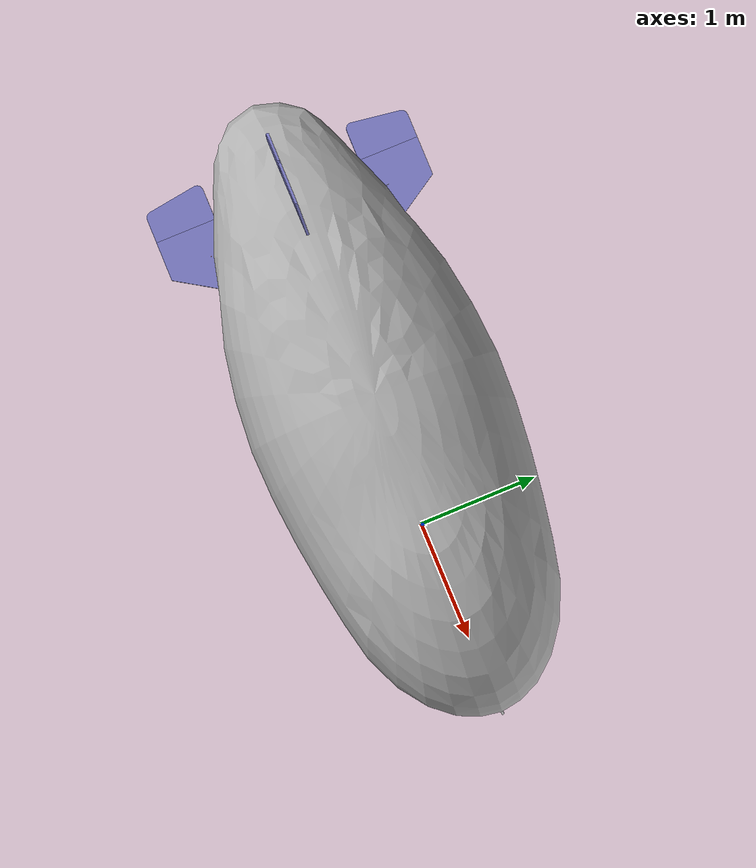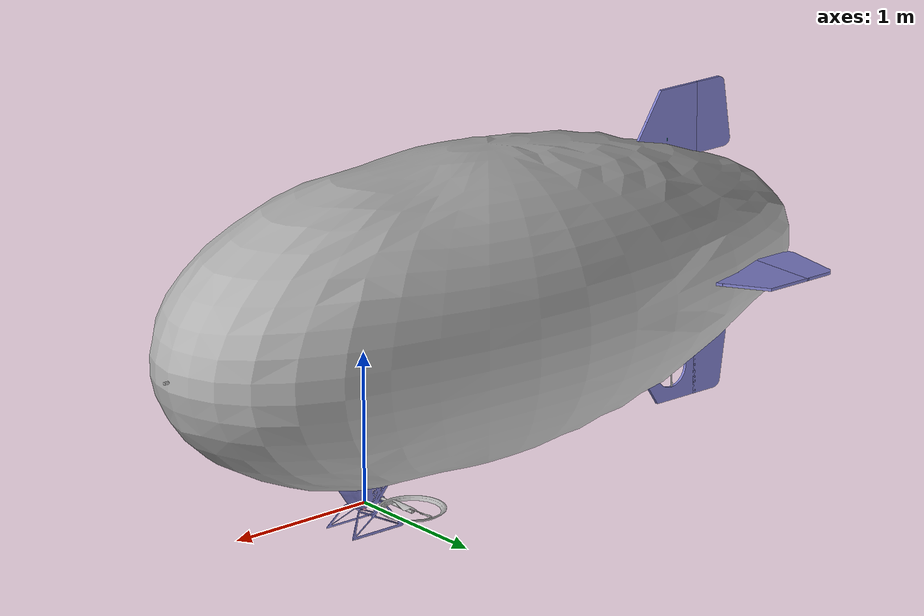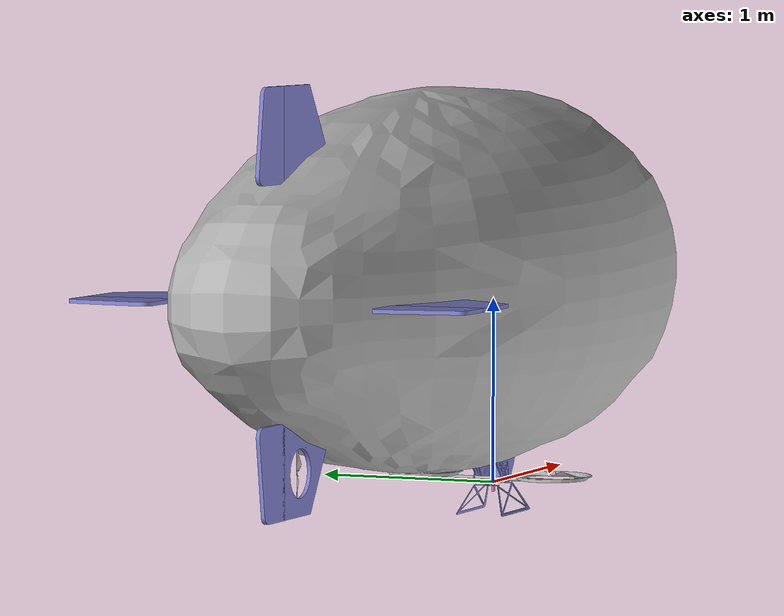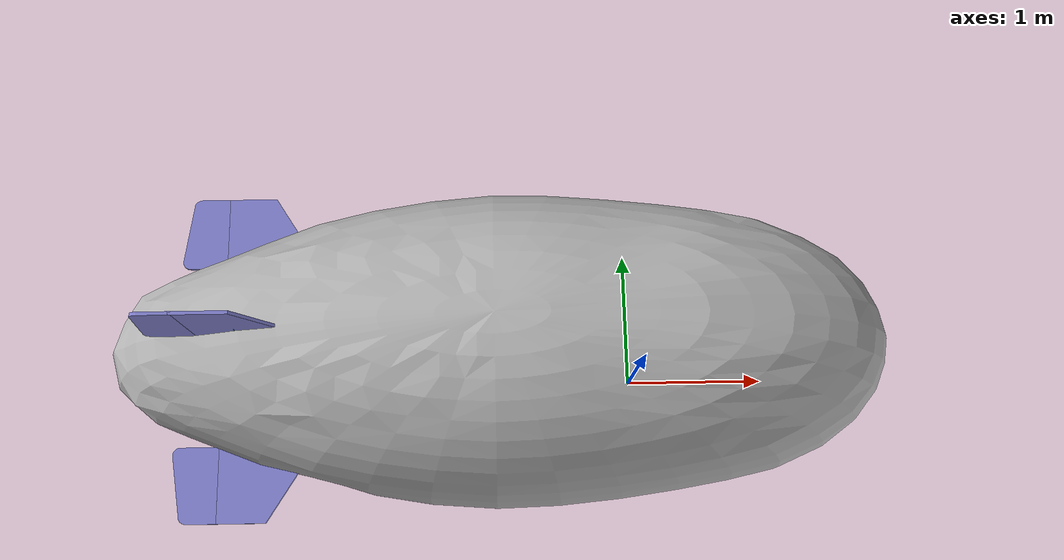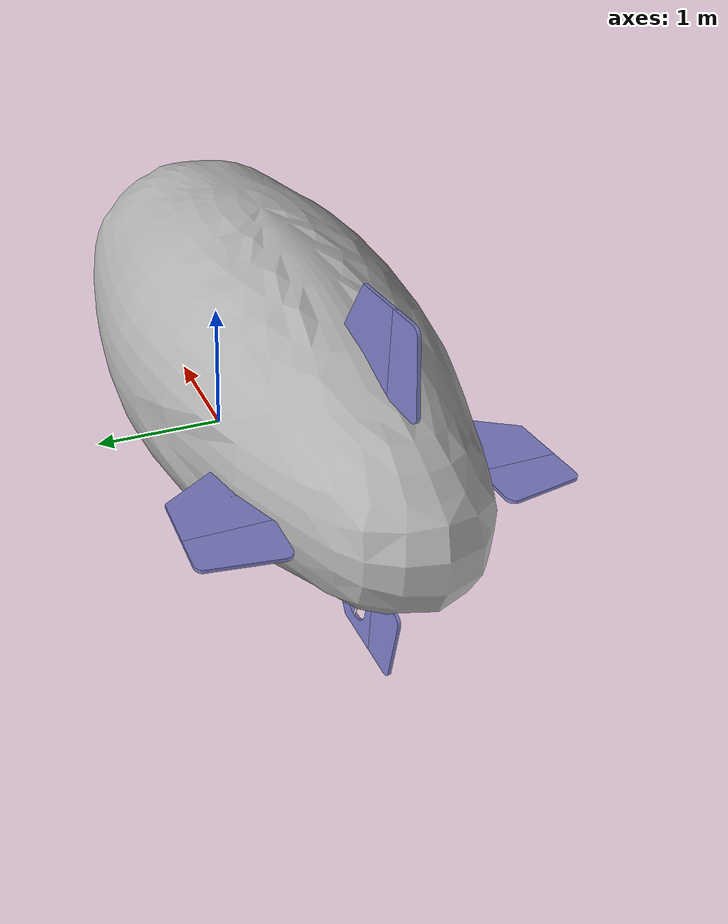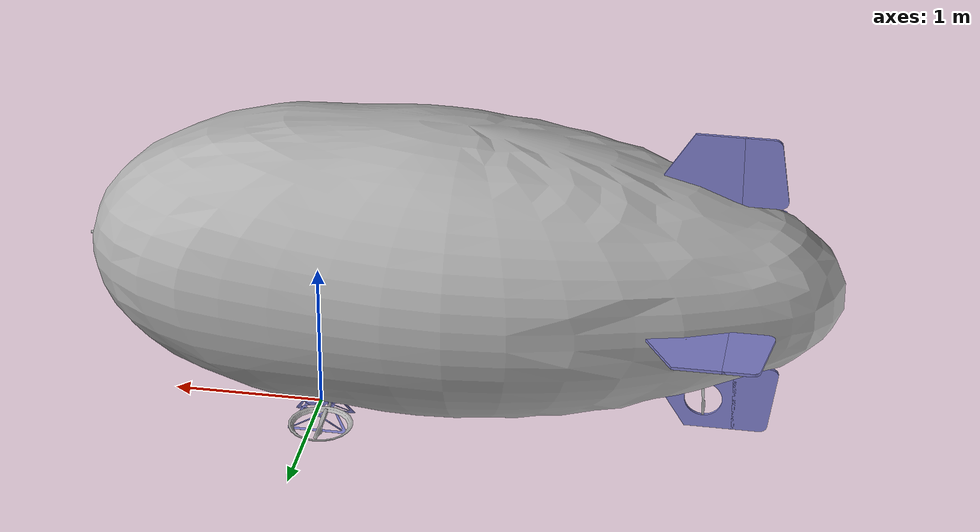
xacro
<?xml version="1.0" ?>
<robot name="blimp" xmlns:xacro="http://ros.org/wiki/xacro">

  <!-- Define M_PI for ROS2 xacro compatibility -->
  <xacro:property name="M_PI" value="3.14159265359" />
  <xacro:property name="PI" value="3.14159265359" />

  <xacro:arg name="namespace" default="blimp"/>
  <xacro:arg name="uav_name" default="blimp"/>

  <!-- FIXED: Added all missing launch arguments that are referenced in included files -->
  <xacro:arg name="enable_custom_plugins" default="true"/>
  <xacro:arg name="enable_meshes" default="true"/>
  <xacro:arg name="enable_wind" default="false"/>
  <xacro:arg name="enable_physics" default="true"/>
  <xacro:arg name="enable_sensors" default="true"/>
  <xacro:arg name="enable_logging" default="false"/>
  <xacro:arg name="enable_ground_truth" default="true"/>
  <xacro:arg name="enable_mavlink_interface" default="false"/>
  <xacro:arg name="log_file" default="blimp"/>
  <xacro:arg name="wait_to_record_bag" default="false"/>
  <xacro:arg name="is_input_joystick" default="false"/>

  <!--*****************  component description  *****************-->
  <xacro:include filename="$(find blimp_description)/urdf/plugin_control.xacro" />
  <xacro:include filename="$(find blimp_description)/urdf/plugin_sensors.xacro" />
  <xacro:include filename="$(find blimp_description)/urdf/plugin_physics.xacro" />

  <!--*****************  property description  *****************-->
  <xacro:include filename="$(find blimp_description)/urdf/description_property.xacro"/>

  <!--*****************  mechanics description   *****************-->
  <xacro:include filename="$(find blimp_description)/urdf/model_xacro.xacro" />
  <xacro:include filename="$(find blimp_description)/urdf/description_link.xacro"/>

  <!--*****************  controller description  *****************-->
  <xacro:include filename="$(find blimp_description)/urdf/description_controller.xacro"/>

  <!--*****************  sensor description  *****************-->
  <xacro:include filename="$(find blimp_description)/urdf/description_sensor.xacro"/>

  <!--*****************  physics and extra plugins description  *****************-->
  <xacro:include filename="$(find blimp_description)/urdf/description_plugin.xacro"/>

  <!-- REMOVED: Duplicate Mavlink plugin definition - now handled in description_sensor.xacro -->

  <!-- ROS 2 Control hardware interface (Gazebo Harmonic) -->
  <gazebo>
    <plugin name="gz_ros2_control::GazeboSimROS2ControlPlugin" filename="gz_ros2_control-system">
      <parameters>$(find blimp_description)/resource/controller_blimp.yaml</parameters>
      <ros>
        <namespace>$(arg namespace)</namespace>
      </ros>
    </plugin>
  </gazebo>

</robot>

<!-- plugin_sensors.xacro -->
<robot xmlns:xacro="http://ros.org/wiki/xacro">

  <!-- ==================== IMU SENSOR MACRO ======================= -->
  <xacro:macro name="imu_plugin_macro"
    params="namespace imu_suffix parent_link imu_topic
      mass_imu_sensor gyroscope_noise_density gyroscope_random_walk
      gyroscope_bias_correlation_time gyroscope_turn_on_bias_sigma
      accelerometer_noise_density accelerometer_random_walk
      accelerometer_bias_correlation_time accelerometer_turn_on_bias_sigma
      *inertia *origin">

    <!-- ✅ FIXED: Attach sensor directly to parent_link, no intermediate links -->
    <gazebo reference="${parent_link}">
      <sensor name="imu_sensor" type="imu">
        <always_on>true</always_on>
        <update_rate>250</update_rate>
        <imu>
          <angular_velocity>
            <x>
              <noise type="gaussian">
                <mean>0.0</mean>
                <stddev>${gyroscope_noise_density}</stddev>
                <bias_mean>0.0</bias_mean>
                <bias_stddev>${gyroscope_turn_on_bias_sigma}</bias_stddev>
                <dynamic_bias_stddev>${gyroscope_random_walk}</dynamic_bias_stddev>
                <dynamic_bias_correlation_time>${gyroscope_bias_correlation_time}</dynamic_bias_correlation_time>
              </noise>
            </x>
            <y>
              <noise type="gaussian">
                <mean>0.0</mean>
                <stddev>${gyroscope_noise_density}</stddev>
                <bias_mean>0.0</bias_mean>
                <bias_stddev>${gyroscope_turn_on_bias_sigma}</bias_stddev>
                <dynamic_bias_stddev>${gyroscope_random_walk}</dynamic_bias_stddev>
                <dynamic_bias_correlation_time>${gyroscope_bias_correlation_time}</dynamic_bias_correlation_time>
              </noise>
            </y>
            <z>
              <noise type="gaussian">
                <mean>0.0</mean>
                <stddev>${gyroscope_noise_density}</stddev>
                <bias_mean>0.0</bias_mean>
                <bias_stddev>${gyroscope_turn_on_bias_sigma}</bias_stddev>
                <dynamic_bias_stddev>${gyroscope_random_walk}</dynamic_bias_stddev>
                <dynamic_bias_correlation_time>${gyroscope_bias_correlation_time}</dynamic_bias_correlation_time>
              </noise>
            </z>
          </angular_velocity>
          <linear_acceleration>
            <x>
              <noise type="gaussian">
                <mean>0.0</mean>
                <stddev>${accelerometer_noise_density}</stddev>
                <bias_mean>0.0</bias_mean>
                <bias_stddev>${accelerometer_turn_on_bias_sigma}</bias_stddev>
                <dynamic_bias_stddev>${accelerometer_random_walk}</dynamic_bias_stddev>
                <dynamic_bias_correlation_time>${accelerometer_bias_correlation_time}</dynamic_bias_correlation_time>
              </noise>
            </x>
            <y>
              <noise type="gaussian">
                <mean>0.0</mean>
                <stddev>${accelerometer_noise_density}</stddev>
                <bias_mean>0.0</bias_mean>
                <bias_stddev>${accelerometer_turn_on_bias_sigma}</bias_stddev>
                <dynamic_bias_stddev>${accelerometer_random_walk}</dynamic_bias_stddev>
                <dynamic_bias_correlation_time>${accelerometer_bias_correlation_time}</dynamic_bias_correlation_time>
              </noise>
            </y>
            <z>
              <noise type="gaussian">
                <mean>0.0</mean>
                <stddev>${accelerometer_noise_density}</stddev>
                <bias_mean>0.0</bias_mean>
                <bias_stddev>${accelerometer_turn_on_bias_sigma}</bias_stddev>
                <dynamic_bias_stddev>${accelerometer_random_walk}</dynamic_bias_stddev>
                <dynamic_bias_correlation_time>${accelerometer_bias_correlation_time}</dynamic_bias_correlation_time>
              </noise>
            </z>
          </linear_acceleration>
        </imu>
        <plugin filename="gz-sim-imu-system" name="gz::sim::systems::Imu">
          <initial_orientation_as_reference>false</initial_orientation_as_reference>
        </plugin>
      </sensor>
    </gazebo>
  </xacro:macro>

  <!-- ==================== GPS SENSOR MACRO ======================= -->
  <xacro:macro name="gps_plugin_macro"
    params="namespace gps_suffix parent_link gps_topic ground_speed_topic
      mass_gps_sensor horizontal_pos_std_dev vertical_pos_std_dev
      horizontal_vel_std_dev vertical_vel_std_dev *inertia *origin">

    <!-- ✅ FIXED: Attach sensor directly to parent_link, no intermediate links -->
    <gazebo reference="${parent_link}">
      <sensor name="navsat_sensor" type="navsat">
        <always_on>true</always_on>
        <update_rate>10.0</update_rate>
        <navsat>
          <position_sensing>
            <horizontal>
              <noise type="gaussian">
                <mean>0.0</mean>
                <stddev>${horizontal_pos_std_dev}</stddev>
              </noise>
            </horizontal>
            <vertical>
              <noise type="gaussian">
                <mean>0.0</mean>
                <stddev>${vertical_pos_std_dev}</stddev>
              </noise>
            </vertical>
          </position_sensing>
          <velocity_sensing>
            <horizontal>
              <noise type="gaussian">
                <mean>0.0</mean>
                <stddev>${horizontal_vel_std_dev}</stddev>
              </noise>
            </horizontal>
            <vertical>
              <noise type="gaussian">
                <mean>0.0</mean>
                <stddev>${vertical_vel_std_dev}</stddev>
              </noise>
            </vertical>
          </velocity_sensing>
        </navsat>
        <plugin filename="gz-sim-navsat-system" name="gz::sim::systems::NavSat">
        </plugin>
      </sensor>
    </gazebo>
  </xacro:macro>

  <!-- =============== MAGNETOMETER SENSOR MACRO =================== -->
  <xacro:macro name="magnetometer_plugin_macro"
    params="namespace magnetometer_suffix parent_link magnetometer_topic
      mass_magnetometer_sensor noise_density *inertia *origin">

    <!-- ✅ FIXED: Attach sensor directly to parent_link, no intermediate links -->
    <gazebo reference="${parent_link}">
      <sensor name="mag_sensor" type="magnetometer">
        <always_on>true</always_on>
        <update_rate>50</update_rate>
        <magnetometer>
          <x>
            <noise type="gaussian">
              <mean>0.0</mean>
              <stddev>${noise_density}</stddev>
            </noise>
          </x>
          <y>
            <noise type="gaussian">
              <mean>0.0</mean>
              <stddev>${noise_density}</stddev>
            </noise>
          </y>
          <z>
            <noise type="gaussian">
              <mean>0.0</mean>
              <stddev>${noise_density}</stddev>
            </noise>
          </z>
        </magnetometer>
        <plugin filename="gz-sim-magnetometer-system" name="gz::sim::systems::Magnetometer">
        </plugin>
      </sensor>
    </gazebo>
  </xacro:macro>

  <!-- =============== PRESSURE SENSOR MACRO ======================= -->
  <xacro:macro name="pressure_sensor_plugin_macro"
    params="namespace pressure_suffix parent_link pressure_topic
      mass_pressure_sensor noise_density *inertia *origin">

    <!-- ✅ FIXED: Attach sensor directly to parent_link, no intermediate links -->
    <gazebo reference="${parent_link}">
      <sensor name="air_pressure_sensor" type="air_pressure">
        <always_on>true</always_on>
        <update_rate>50</update_rate>
        <air_pressure>
          <reference_altitude>341</reference_altitude>
          <noise type="gaussian">
            <mean>0.0</mean>
            <stddev>${noise_density}</stddev>
          </noise>
        </air_pressure>
        <plugin filename="gz-sim-air-pressure-system" name="gz::sim::systems::AirPressure">
        </plugin>
      </sensor>
    </gazebo>
  </xacro:macro>

  <!-- ==================== ODOMETRY MACRO ========================= -->
  <xacro:macro name="odometry_plugin_macro"
    params="namespace odometry_sensor_suffix parent_link pose_topic
      pose_with_covariance_topic position_topic transform_topic odometry_topic
      parent_frame_id child_frame_id mass_odometry_sensor measurement_divisor
      measurement_delay unknown_delay noise_normal_position noise_normal_quaternion
      noise_normal_linear_velocity noise_normal_angular_velocity noise_uniform_position
      noise_uniform_quaternion noise_uniform_linear_velocity noise_uniform_angular_velocity
      enable_odometry_map odometry_map image_scale *inertia *origin">

    <!-- ✅ ROS2 Odometry (separate from PX4 sensor discovery) -->
    <gazebo reference="${parent_link}">
      <plugin filename="gz-sim-odometry-publisher-system" name="gz::sim::systems::OdometryPublisher">
        <ros>
          <namespace>${namespace}</namespace>
          <remapping>~/out:=${odometry_topic}</remapping>
        </ros>
        <odom_frame>${parent_frame_id}</odom_frame>
        <robot_base_frame>${child_frame_id}</robot_base_frame>
        <odom_publish_frequency>100</odom_publish_frequency>
        <odom_covariance_x>0.0001</odom_covariance_x>
        <odom_covariance_y>0.0001</odom_covariance_y>
        <odom_covariance_yaw>0.01</odom_covariance_yaw>
      </plugin>
    </gazebo>
  </xacro:macro>

  <!-- ==================== CONVENIENCE MACROS ==================== -->

  <xacro:macro name="ground_truth_imu_and_odometry" params="namespace parent_link">
    <!-- Mount an IMU providing ground truth. -->
    <xacro:imu_plugin_macro
      namespace="${namespace}"
      imu_suffix="_gt"
      parent_link="${parent_link}"
      imu_topic="ground_truth/imu"
      mass_imu_sensor="0.00001"
      gyroscope_noise_density="0.0"
      gyroscope_random_walk="0.0"
      gyroscope_bias_correlation_time="1000.0"
      gyroscope_turn_on_bias_sigma="0.0"
      accelerometer_noise_density="0.0"
      accelerometer_random_walk="0.0"
      accelerometer_bias_correlation_time="300.0"
      accelerometer_turn_on_bias_sigma="0.0">
      <inertia ixx="0.00001" ixy="0.0" ixz="0.0" iyy="0.00001" iyz="0.0" izz="0.00001" />
      <origin xyz="0 0 0" rpy="0 0 0" />
    </xacro:imu_plugin_macro>

    <!-- Mount a generic odometry sensor providing ground truth. -->
    <xacro:odometry_plugin_macro
      namespace="${namespace}"
      odometry_sensor_suffix="_gt"
      parent_link="${parent_link}"
      pose_topic="ground_truth/pose"
      pose_with_covariance_topic="ground_truth/pose_with_covariance"
      position_topic="ground_truth/position"
      transform_topic="ground_truth/transform"
      odometry_topic="ground_truth/odometry"
      parent_frame_id="world"
      child_frame_id="base_link"
      mass_odometry_sensor="0.00001"
      measurement_divisor="1"
      measurement_delay="0"
      unknown_delay="0.0"
      noise_normal_position="0 0 0"
      noise_normal_quaternion="0 0 0"
      noise_normal_linear_velocity="0 0 0"
      noise_normal_angular_velocity="0 0 0"
      noise_uniform_position="0 0 0"
      noise_uniform_quaternion="0 0 0"
      noise_uniform_linear_velocity="0 0 0"
      noise_uniform_angular_velocity="0 0 0"
      enable_odometry_map="false"
      odometry_map=""
      image_scale="">
      <inertia ixx="0.00001" ixy="0.0" ixz="0.0" iyy="0.00001" iyz="0.0" izz="0.00001" />
      <origin xyz="0.0 0.0 0.0" rpy="0.0 0.0 0.0" />
    </xacro:odometry_plugin_macro>
  </xacro:macro>

  <xacro:macro name="tail_imu_and_odometry" params="namespace parent_link">
    <!-- Mount an IMU for tail. -->
    <xacro:imu_plugin_macro
      namespace="${namespace}"
      imu_suffix="_tail"
      parent_link="${parent_link}"
      imu_topic="tail/imu"
      mass_imu_sensor="0.00001"
      gyroscope_noise_density="0.0"
      gyroscope_random_walk="0.0"
      gyroscope_bias_correlation_time="1000.0"
      gyroscope_turn_on_bias_sigma="0.0"
      accelerometer_noise_density="0.0"
      accelerometer_random_walk="0.0"
      accelerometer_bias_correlation_time="300.0"
      accelerometer_turn_on_bias_sigma="0.0">
      <inertia ixx="0.00001" ixy="0.0" ixz="0.0" iyy="0.00001" iyz="0.0" izz="0.00001" />
      <origin xyz="0 0 0" rpy="${pi} 0 0" />
    </xacro:imu_plugin_macro>

    <!-- Mount a generic odometry sensor for tail. -->
    <xacro:odometry_plugin_macro
      namespace="${namespace}"
      odometry_sensor_suffix="_tail"
      parent_link="${parent_link}"
      pose_topic="tail/pose"
      pose_with_covariance_topic="tail/pose_with_covariance"
      position_topic="tail/position"
      transform_topic="tail/transform"
      odometry_topic="tail/odometry"
      parent_frame_id="world"
      child_frame_id="${parent_link}"
      mass_odometry_sensor="0.00001"
      measurement_divisor="1"
      measurement_delay="0"
      unknown_delay="0.0"
      noise_normal_position="0 0 0"
      noise_normal_quaternion="0 0 0"
      noise_normal_linear_velocity="0 0 0"
      noise_normal_angular_velocity="0 0 0"
      noise_uniform_position="0 0 0"
      noise_uniform_quaternion="0 0 0"
      noise_uniform_linear_velocity="0 0 0"
      noise_uniform_angular_velocity="0 0 0"
      enable_odometry_map="false"
      odometry_map=""
      image_scale="">
      <inertia ixx="0.00001" ixy="0.0" ixz="0.0" iyy="0.00001" iyz="0.0" izz="0.00001" />
      <origin xyz="0.0 0.0 0.0" rpy="${pi} 0.0 0.0" />
    </xacro:odometry_plugin_macro>
  </xacro:macro>

  <!-- ✅ PRIMARY FLIGHT CONTROL SENSORS (attach directly to parent_link) -->
  <xacro:macro name="default_imu" params="namespace parent_link">
    <!-- ADIS16448 IMU for PX4 flight control -->
    <xacro:imu_plugin_macro
      namespace="${namespace}"
      imu_suffix=""
      parent_link="${parent_link}"
      imu_topic="imu"
      mass_imu_sensor="0.015"
      gyroscope_noise_density="0.0003394"
      gyroscope_random_walk="0.000038785"
      gyroscope_bias_correlation_time="1000.0"
      gyroscope_turn_on_bias_sigma="0.0087"
      accelerometer_noise_density="0.004"
      accelerometer_random_walk="0.006"
      accelerometer_bias_correlation_time="300.0"
      accelerometer_turn_on_bias_sigma="0.1960">
      <inertia ixx="0.00001" ixy="0.0" ixz="0.0" iyy="0.00001" iyz="0.0" izz="0.00001" />
      <origin xyz="0 0 0" rpy="0 0 0" />
    </xacro:imu_plugin_macro>
  </xacro:macro>

  <xacro:macro name="default_gps" params="namespace parent_link">
    <!-- GPS for PX4 navigation -->
    <xacro:gps_plugin_macro
      namespace="${namespace}"
      gps_suffix=""
      parent_link="${parent_link}"
      gps_topic="gps"
      ground_speed_topic="ground_speed"
      mass_gps_sensor="0.015"
      horizontal_pos_std_dev="3.0"
      vertical_pos_std_dev="6.0"
      horizontal_vel_std_dev="0.1"
      vertical_vel_std_dev="0.1">
      <inertia ixx="0.00001" ixy="0.0" ixz="0.0" iyy="0.00001" iyz="0.0" izz="0.00001" />
      <origin xyz="0 0 0" rpy="0 0 0" />
    </xacro:gps_plugin_macro>
  </xacro:macro>

  <xacro:macro name="default_magnetometer" params="namespace parent_link">
    <!-- Magnetometer for PX4 heading estimation -->
    <xacro:magnetometer_plugin_macro
      namespace="${namespace}"
      magnetometer_suffix=""
      parent_link="${parent_link}"
      magnetometer_topic="magnetic_field"
      mass_magnetometer_sensor="0.005"
      noise_density="0.0004">
      <inertia ixx="0.00001" ixy="0.0" ixz="0.0" iyy="0.00001" iyz="0.0" izz="0.00001" />
      <origin xyz="0 0 0" rpy="0 0 0" />
    </xacro:magnetometer_plugin_macro>
  </xacro:macro>

  <xacro:macro name="default_pressure_sensor" params="namespace parent_link">
    <!-- Barometer for PX4 altitude estimation -->
    <xacro:pressure_sensor_plugin_macro
      namespace="${namespace}"
      pressure_suffix=""
      parent_link="${parent_link}"
      pressure_topic="air_pressure"
      mass_pressure_sensor="0.005"
      noise_density="0.01">
      <inertia ixx="0.00001" ixy="0.0" ixz="0.0" iyy="0.00001" iyz="0.0" izz="0.00001" />
      <origin xyz="0 0 0" rpy="0 0 0" />
    </xacro:pressure_sensor_plugin_macro>
  </xacro:macro>

</robot>

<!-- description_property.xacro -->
<robot xmlns:xacro="http://ros.org/wiki/xacro">
  <!--***************** property description  *****************-->
  <xacro:property name="namespace" value="$(arg uav_name)" />
  <xacro:property name="air_density" value="1.2041"/> <!--[kg/m^3] Temperature 20celsius: 1.2041-->

  <!-- meshes - FIXED: Use file:// paths for Gazebo Harmonic compatibility -->
  <xacro:property name="use_mesh_file" value="$(arg enable_meshes)" />
  <xacro:property name="mesh_file_blimp_body" value="file://$(find blimp_description)/meshes/blimp_body/blimp_body_v4.dae" />
  <xacro:property name="mesh_file_blimp_support" value="file://$(find blimp_description)/meshes/blimp_support/blimp_support_v5.dae" />
  <xacro:property name="mesh_file_blimp_gondola" value="file://$(find blimp_description)/meshes/blimp_gondola/blimp_gondola_v4.dae" />
  <xacro:property name="mesh_file_blimp_wing" value="file://$(find blimp_description)/meshes/blimp_wing/blimp_wing_v2.dae" />
  <xacro:property name="mesh_file_blimp_stick" value="file://$(find blimp_description)/meshes/blimp_wing/blimp_stick_v2.dae" />
  <xacro:property name="mesh_file_propeller_cw" value="file://$(find blimp_description)/meshes/blimp_propeller/blimp_right_propeller_cw_v3.dae" />
  <xacro:property name="mesh_file_propeller_ccw" value="file://$(find blimp_description)/meshes/blimp_propeller/blimp_left_propeller_ccw_v3.dae" />
  <xacro:property name="mesh_file_bot_propeller_cw" value="file://$(find blimp_description)/meshes/blimp_propeller/blimp_bot_propeller_cw_v3.dae" />
  <xacro:property name="mesh_file_blimp_rud_part1" value="file://$(find blimp_description)/meshes/blimp_fin/blimp_top_rud_part1_v3.dae" />
  <xacro:property name="mesh_file_blimp_rud_part2" value="file://$(find blimp_description)/meshes/blimp_fin/blimp_top_rud_part2_v5.dae" />
  <xacro:property name="mesh_file_blimp_bot_rud_part1" value="file://$(find blimp_description)/meshes/blimp_fin/blimp_bot_rud_part1_v3.dae" />

  <!-- Volume and gas properties -->
  <xacro:property name="volume_total" value="${volume_blimp_body}" />
  <xacro:property name="helium_mass" value="1.723" /> <!-- kg -->

  <!-- Sensor noise parameters for Gazebo Harmonic -->
  <xacro:property name="gyroscope_noise_density" value="0.0003394" />
  <xacro:property name="gyroscope_random_walk" value="0.000038785" />
  <xacro:property name="gyroscope_bias_correlation_time" value="1000.0" />
  <xacro:property name="gyroscope_turn_on_bias_sigma" value="0.0087" />
  <xacro:property name="accelerometer_noise_density" value="0.004" />
  <xacro:property name="accelerometer_random_walk" value="0.006" />
  <xacro:property name="accelerometer_bias_correlation_time" value="300.0" />
  <xacro:property name="accelerometer_turn_on_bias_sigma" value="0.1960" />

  <!-- Additional missing fin definitions -->
  <xacro:property name="area_fin_total" value="${area_fin * 6}" /> <!-- 6 fins total -->
  <xacro:property name="area_body_side" value="5.0" /> <!-- Side projection area -->

  <!-- Gazebo Harmonic controller parameters -->
  <xacro:property name="controller_update_rate" value="100" /> <!-- Hz -->

  <!-- mass [kg] -->
  <!-- Modified mass for convenience -->
  <xacro:property name="mass_blimp_body" value="4.622" />
  <xacro:property name="mass_blimp_body_without_gas" value="2.90" />
  <xacro:property name="mass_gondola_body" value="1.105" /> <!--battery: 0.51kg + body:0.595kg = 1.105-->
  <!--battery: 0.25kg + body:0.595kg = 0.845-->
  <xacro:property name="mass_gondola_support" value="0.2" /> <!--guessed 0.2kg-->
  <xacro:property name="mass_stick" value="0.705" />
  <xacro:property name="mass_wing" value="0.500" /> <!--guessed 0.5kg-->
  <xacro:property name="mass_blade" value="0.050" />
  <xacro:property name="mass_rud_part1" value="0.58" /> <!--part1: 0.162kg + wire: 0.097kg = 0.259 -->
  <xacro:property name="mass_rud_part2" value="0.113" />
  <xacro:property name="mass_bot_rud_part1" value="0.410" /> <!--part1: 0.120kg + wire: 0.290kg = 0.410 -->
  <xacro:property name="mass_bot_rud_motor" value="0.127" />
  <xacro:property name="mass_ballast" value="0.4" />

  <!-- geometry [m] -->
  <xacro:property name="radius_blimp_body" value="1.00"/>
  <xacro:property name="length_blimp_body" value="5.00"/>
  <xacro:property name="volume_blimp_body" value="10.472"/>
  <xacro:property name="length_blimp_skin" value="0.0002"/>
  <xacro:property name="length_gondola_body" value="0.420"/>
  <xacro:property name="width_gondola_body" value="0.160"/>
  <xacro:property name="height_gondola_body" value="0.200"/>
  <xacro:property name="length_gondola_support" value="0.420"/>
  <xacro:property name="width_gondola_support" value="0.020"/>
  <xacro:property name="height_gondola_support" value="0.200"/>
  <xacro:property name="radius_stick" value="0.010"/>
  <xacro:property name="length_stick" value="0.750"/>
  <xacro:property name="radius_wing" value="0.215"/>
  <xacro:property name="length_wing" value="0.030"/>
  <xacro:property name="length_wing_skin" value="0.015"/>
  <xacro:property name="radius_blade" value="0.010"/>
  <xacro:property name="length_blade" value="0.390"/>
  <xacro:property name="length_rud_part1" value="0.55"/>
  <xacro:property name="width_rud_part1" value="0.02"/>
  <xacro:property name="height_rud_part1" value="0.48"/>
  <xacro:property name="length_rud_part2" value="0.30"/>
  <xacro:property name="width_rud_part2" value="0.02"/>
  <xacro:property name="height_rud_part2" value="0.48"/>
  <xacro:property name="radius_bot_rud_motor" value="0.005"/>
  <xacro:property name="length_bot_rud_motor" value="0.250"/>
  <xacro:property name="radius_ballast" value="0.01"/>
  <xacro:property name="length_ballast" value="0.05"/>

  <!-- joint parameters -->
  <xacro:property name="flex_joint_flexibility_factor" value="1.0" />
  <xacro:property name="flex_joint_flexibility_damping" value="0.5" />
  <xacro:property name="flex_joint_flexibility_friction" value="0" />
  <xacro:property name="rotor_velocity_slowdown_sim" value="1" />
  <xacro:property name="rotor_offset_top" value="0.05" />
  <xacro:property name="motor_constant" value="3.71178707e-03" /> <!-- [kg m/s^2] -->
  <xacro:property name="moment_constant" value="0.016" />
  <!-- FIXED: Original ROS1 motor time constants for realistic motor dynamics -->
  <xacro:property name="time_constant_up" value="0.05" />
  <xacro:property name="time_constant_down" value="0.08" />
  <xacro:property name="max_rot_velocity" value="879.23" /> <!-- [rad/s] -->
  <xacro:property name="rotor_drag_coefficient" value="8.06428e-05" />
  <xacro:property name="rolling_moment_coefficient" value="0.000001" />
  <xacro:property name="area_blade" value="0.0078"/>
  <xacro:property name="effort_stick" value="1000"/>
  <xacro:property name="velocity_stick" value="2"/> <!-- [rad/s] -->
  <xacro:property name="max_angle_stick" value="${100 * pi /180.0 }"/> <!-- [rad] -->
  <xacro:property name="effort_fin" value="500"/>
  <xacro:property name="velocity_fin" value="2"/> <!-- [rad/s] -->
  <xacro:property name="max_angle_fin" value="${60 * pi /180.0 }"/> <!-- [rad] 0.087-->
  <xacro:property name="area_fin" value="0.16"/>
  <xacro:property name="area_fin_front" value="0.01"/>
  <xacro:property name="area_rudder" value="0.16"/>
  <xacro:property name="area_body_lift" value="3.14"/>
  <xacro:property name="area_body_front" value="3.14"/>

  <!-- inertia [kg m^2] [kg m^2] [kg m^2] [kg m^2] [kg m^2] [kg m^2] -->
  <xacro:include filename="$(find blimp_description)/urdf/inertia_calculator.xacro"/>
  <xacro:property name="inertia_blimp_body">
        <xacro:hollow_cylinder_inertia r1="${radius_blimp_body - length_blimp_skin}" r2="${radius_blimp_body}" h="${length_blimp_body}" mass="${mass_blimp_body_without_gas}"/> <!--TODO: better use hollow ellipse-->
  </xacro:property>
  <xacro:property name="inertia_gondola_body">
        <xacro:cuboid_inertia x="${length_gondola_body}" y="${width_gondola_body}" z="${height_gondola_body}" mass="${mass_gondola_body}"/>
  </xacro:property>
  <xacro:property name="inertia_gondola_support">
        <xacro:cuboid_inertia x="${length_gondola_support}" y="${width_gondola_support}" z="${height_gondola_support}" mass="${mass_gondola_support}"/>
  </xacro:property>
  <xacro:property name="inertia_stick">
        <xacro:cylinder_inertia r="${radius_stick}" h="${length_stick}" mass="${mass_stick}"/>
  </xacro:property>
  <xacro:property name="inertia_wing">
        <xacro:hollow_cylinder_inertia r1="${radius_wing - length_wing_skin}" r2="${radius_wing}" h="${length_wing}" mass="${mass_wing}"/>
  </xacro:property>
  <xacro:property name="inertia_blade">
        <xacro:cylinder_inertia r="${radius_blade}" h="${length_blade}" mass="${mass_blade*rotor_velocity_slowdown_sim}"/>
  </xacro:property>
  <xacro:property name="inertia_rud_part1">
        <xacro:cuboid_inertia x="${length_rud_part1}" y="${width_rud_part1}" z="${height_rud_part1}" mass="${mass_rud_part1}"/>
  </xacro:property>
  <xacro:property name="inertia_rud_part2">
        <xacro:cuboid_inertia x="${length_rud_part2}" y="${width_rud_part2}" z="${height_rud_part2}" mass="${mass_rud_part2}"/>
  </xacro:property>
  <!-- FIXED: Added missing separate bot rudder part1 inertia from original ROS1 -->
  <xacro:property name="inertia_bot_rud_part1">
        <xacro:cuboid_inertia x="${length_rud_part1}" y="${width_rud_part1}" z="${height_rud_part1}" mass="${mass_bot_rud_part1}"/>
  </xacro:property>
  <xacro:property name="inertia_bot_rud_motor">
        <xacro:cylinder_inertia r="${radius_bot_rud_motor}" h="${length_bot_rud_motor}" mass="${mass_bot_rud_motor*rotor_velocity_slowdown_sim}"/>
  </xacro:property>
  <xacro:property name="inertia_ballast">
        <xacro:cylinder_inertia r="${radius_ballast}" h="${length_ballast}" mass="${mass_ballast}"/>
  </xacro:property>

  <!-- visual origins -->
  <xacro:property name="origin_blimp_body">
    <origin xyz="0  0  0" rpy="0  0  0"/>
  </xacro:property>
  <xacro:property name="origin_gondola_body">
    <origin xyz="0  0  0" rpy="0  0  0"/>
  </xacro:property>
  <xacro:property name="origin_gondola_support">
    <origin xyz="0  0  0" rpy="0  0  0"/>
  </xacro:property>
  <xacro:property name="origin_stick">
    <origin xyz="0  0  0" rpy="0  0  0"/>
  </xacro:property>
  <xacro:property name="origin_wing">
    <origin xyz="0  0  0" rpy="0  0  0"/>
  </xacro:property>
  <xacro:property name="origin_blade">
    <origin xyz="0  0  0" rpy="${pi/2}  0  0"/>
  </xacro:property>
  <xacro:property name="origin_rud_part1">
    <origin xyz="0  0  0" rpy="0  0  0"/>
  </xacro:property>
  <xacro:property name="origin_rud_part2">
    <origin xyz="0  0  0" rpy="0  0  0"/>
  </xacro:property>
  <xacro:property name="origin_bot_rud_part1">
    <origin xyz="0  0  0" rpy="0  0  0"/>
  </xacro:property>
  <xacro:property name="origin_bot_rud_motor">
    <origin xyz="0  0  0" rpy="0  0  0"/>
  </xacro:property>
  <xacro:property name="origin_ballast">
    <origin xyz="0  0  0" rpy="0  0  0"/>
  </xacro:property>

  <!-- FIXED: Correct joint origins from original ROS1 implementation -->
  <!-- joint origins [m] [m] [m] [rad] [rad] [rad] -->
  <xacro:property name="origin_blimp_body_forward_lift_joint">
    <origin xyz="0 0 2.0" rpy="0.0 ${-pi/2} ${pi/2}"/>
  </xacro:property>
  <xacro:property name="origin_blimp_body_aft_lift_joint">
    <origin xyz="0 0 -0.3" rpy="0.0 ${-pi/2} ${pi/2}"/>
  </xacro:property>
  <xacro:property name="origin_base_gondola_body_joint">
    <origin xyz="0 0 0.10" rpy="0 0 0"/>
  </xacro:property>
  <xacro:property name="origin_base_gondola_left_support_joint">
    <origin xyz="0.0 0.1 -0.085" rpy="0.4 0.0 0.0"/>
  </xacro:property>
  <xacro:property name="origin_base_gondola_right_support_joint">
    <origin xyz="0.0 -0.1 -0.085" rpy="0.4 0.0 ${pi}"/>
  </xacro:property>
  <xacro:property name="origin_gondola_body_joint_link_joint">
    <origin xyz="0.0 0.0 0.0" rpy="0.0 0.0 0.0"/>
  </xacro:property>
  <xacro:property name="origin_gondola_joint_blimp_body_joint">
    <origin xyz="-1.00 0.0 1.05" rpy="0.0 ${pi/2} 0.0"/>
  </xacro:property>
  <xacro:property name="origin_blimp_body_front_ballast_joint">
    <origin xyz="0.0 0.0 2.5" rpy="0.0 0.0 0.0"/>
  </xacro:property>
  <xacro:property name="origin_base_stick_joint">
    <origin xyz="-0.08 0 0.03" rpy="${pi/2} 0.0 0.0"/>
  </xacro:property>
  <xacro:property name="origin_stick_left_wing_joint">
    <origin xyz="0.0 0.02 -0.375" rpy="${-pi/2} 0.0 0.0"/>
  </xacro:property>
  <xacro:property name="origin_stick_right_wing_joint">
    <origin xyz="0.0 0.02 0.375" rpy="${-pi/2} 0.0 0.0"/>
  </xacro:property>
  <xacro:property name="origin_stick_left_blade_joint">
    <origin xyz="0.0 0.025 -0.375" rpy="${-pi/2} 0.0 0.0"/>
  </xacro:property>
  <xacro:property name="origin_stick_right_blade_joint">
     <origin xyz="0.0 0.025 0.375" rpy="${-pi/2} 0.0 0.0"/>
  </xacro:property>

  <!-- FIXED: Original ROS1 rudder and elevator positioning -->
  <xacro:property name="origin_top_rud_base_link_joint">
    <origin xyz="-0.59 0.0 -1.5" rpy="${pi} ${-pi/2} 0.0"/>
  </xacro:property>
  <xacro:property name="origin_blimp_body_top_rud_part1_joint">
    <origin xyz="0.0 0.0 -0.24" rpy="0.0 0.0 0.0"/>
  </xacro:property>
  <xacro:property name="origin_top_rud_part1_top_rud_joint_link_joint">
    <origin xyz="-0.28 0.0 0.0" rpy="0.0 0.0 0.0"/>
  </xacro:property>
  <xacro:property name="origin_top_rud_joint_link_top_rud_part2_joint">
    <origin xyz="-0.125 0.0 0.0" rpy="0.0 0.0 0.0"/>
  </xacro:property>

  <xacro:property name="origin_bot_rud_base_link_joint">
    <origin xyz="0.59 0.0 -1.5" rpy="0.0 ${-pi/2} 0.0"/>
  </xacro:property>
  <xacro:property name="origin_blimp_body_bot_rud_part1_joint">
    <origin xyz="0.0 0.0 -0.24" rpy="0.0 0.0 0.0"/>
  </xacro:property>
  <xacro:property name="origin_bot_rud_part1_bot_rud_joint_link_joint">
    <origin xyz="-0.28 0.0 0.0" rpy="0.0 0.0 0.0"/>
  </xacro:property>
  <xacro:property name="origin_bot_rud_joint_link_bot_rud_part2_joint">
    <origin xyz="-0.125 0.0 0.0" rpy="0.0 0.0 0.0"/>
  </xacro:property>
  <xacro:property name="origin_bot_rud_part1_bot_rud_motor_joint">
    <origin xyz="-0.065 0.01 -0.025" rpy="${-pi/2} 0.0 0.0"/>
  </xacro:property>

  <xacro:property name="origin_left_elv_base_link_joint">
    <origin xyz="0.0 0.59 -1.5" rpy="0.0 ${-pi/2} ${pi/2}"/>
  </xacro:property>
  <xacro:property name="origin_blimp_body_left_elv_part1_joint">
    <origin xyz="0.0 0.0 -0.24" rpy="0.0 0.0 0.0"/>
  </xacro:property>
  <xacro:property name="origin_left_elv_part1_left_elv_joint_link_joint">
    <origin xyz="-0.28 0.0 0.0" rpy="0.0 0.0 0.0"/>
  </xacro:property>
  <xacro:property name="origin_left_elv_joint_link_left_elv_part2_joint">
    <origin xyz="-0.125 0.0 0.0" rpy="0.0 0.0 0.0"/>
  </xacro:property>

  <xacro:property name="origin_right_elv_base_link_joint">
    <origin xyz="0.0 -0.59 -1.5" rpy="0.0 ${-pi/2} ${-pi/2}"/>
  </xacro:property>
  <xacro:property name="origin_blimp_body_right_elv_part1_joint">
    <origin xyz="0.0 0.0 -0.24" rpy="0.0 0.0 0.0"/>
  </xacro:property>
  <xacro:property name="origin_right_elv_part1_right_elv_joint_link_joint">
    <origin xyz="-0.28 0.0 0.0" rpy="0.0 0.0 0.0"/>
  </xacro:property>
  <xacro:property name="origin_right_elv_joint_link_right_elv_part2_joint">
    <origin xyz="-0.125 0.0 0.0" rpy="0.0 0.0 0.0"/>
  </xacro:property>

</robot>

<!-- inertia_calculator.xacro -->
<robot xmlns:xacro="http://ros.org/wiki/xacro">

  <!-- ==================== BASIC INERTIA CALCULATORS ============== -->

  <!-- Solid cylinder inertia -->
  <xacro:macro name="cylinder_inertia" params="r h mass">
    <inertia ixx="${mass*(3*r*r+h*h)/12}" ixy="0" ixz="0"
             iyy="${mass*(3*r*r+h*h)/12}" iyz="0"
             izz="${mass*r*r/2}" />
  </xacro:macro>

  <!-- Hollow cylinder inertia -->
  <xacro:macro name="hollow_cylinder_inertia" params="r1 r2 h mass">
    <inertia ixx="${mass*(3*(r2*r2+r1*r1)+h*h)/12}" ixy="0" ixz="0"
             iyy="${mass*(3*(r2*r2+r1*r1)+h*h)/12}" iyz="0"
             izz="${mass*(r2*r2+r1*r1)/2}" />
  </xacro:macro>

  <!-- Solid sphere inertia -->
  <xacro:macro name="sphere_inertia" params="r mass">
    <inertia ixx="${2*mass*r*r/5}" ixy="0" ixz="0"
             iyy="${2*mass*r*r/5}" iyz="0"
             izz="${2*mass*r*r/5}" />
  </xacro:macro>

  <!-- Solid box/cuboid inertia -->
  <xacro:macro name="cuboid_inertia" params="x y z mass">
    <inertia ixx="${mass*(y*y+z*z)/12}" ixy="0" ixz="0"
             iyy="${mass*(x*x+z*z)/12}" iyz="0"
             izz="${mass*(x*x+y*y)/12}" />
  </xacro:macro>

  <!-- Ellipsoid inertia -->
  <xacro:macro name="ellipsoid_inertia" params="a b c mass">
    <inertia ixx="${mass*(b*b+c*c)/5}" ixy="0" ixz="0"
             iyy="${mass*(a*a+c*c)/5}" iyz="0"
             izz="${mass*(a*a+b*b)/5}" />
  </xacro:macro>

</robot>

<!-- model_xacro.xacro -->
<robot xmlns:xacro="http://ros.org/wiki/xacro">

  <!-- ==================== BASIC GEOMETRY MACROS ================== -->

  <!-- Cylinder model macro -->
  <xacro:macro name="cylinder_model"
    params="robot_namespace link_name mass body_radius body_length
            use_mesh_file mesh_file *origin *inertia">
    <link name="${link_name}_link">
      <inertial>
        <mass value="${mass}"/>
        <xacro:insert_block name="origin" />
        <xacro:insert_block name="inertia" />
      </inertial>

      <visual>
        <xacro:insert_block name="origin" />
        <geometry>
          <xacro:if value="${use_mesh_file}">
            <mesh filename="${mesh_file}" scale="1 1 1"/>
          </xacro:if>
          <xacro:unless value="${use_mesh_file}">
            <cylinder radius="${body_radius}" length="${body_length}"/>
          </xacro:unless>
        </geometry>
        <material name="${link_name}_material">
          <color rgba="0.7 0.7 0.7 1.0"/>
        </material>
      </visual>

      <collision>
        <xacro:insert_block name="origin" />
        <geometry>
          <xacro:if value="${use_mesh_file}">
            <!-- Use simplified collision geometry for better performance -->
            <cylinder radius="${body_radius}" length="${body_length}"/>
          </xacro:if>
          <xacro:unless value="${use_mesh_file}">
            <cylinder radius="${body_radius}" length="${body_length}"/>
          </xacro:unless>
        </geometry>
      </collision>
    </link>
    <gazebo reference="${link_name}_link">
      <kp>1000000.0</kp>
      <kd>1000000.0</kd>
      <mu1>10.0</mu1>
      <mu2>10.0</mu2>
    </gazebo>
  </xacro:macro>

  <!-- Box model macro -->
  <xacro:macro name="box_model"
    params="robot_namespace link_name mass body_length body_width body_height
            use_mesh_file mesh_file *origin *inertia">
    <link name="${link_name}_link">
      <inertial>
        <mass value="${mass}"/>
        <xacro:insert_block name="origin" />
        <xacro:insert_block name="inertia" />
      </inertial>

      <visual>
        <xacro:insert_block name="origin" />
        <geometry>
          <xacro:if value="${use_mesh_file}">
            <mesh filename="${mesh_file}" scale="1 1 1"/>
          </xacro:if>
          <xacro:unless value="${use_mesh_file}">
            <box size="${body_length} ${body_width} ${body_height}"/>
          </xacro:unless>
        </geometry>
        <material name="${link_name}_material">
          <color rgba="0.5 0.5 0.8 1.0"/>
        </material>
      </visual>

      <collision>
        <xacro:insert_block name="origin" />
        <geometry>
          <xacro:if value="${use_mesh_file}">
            <!-- Use simplified collision geometry for better performance -->
            <box size="${body_length} ${body_width} ${body_height}"/>
          </xacro:if>
          <xacro:unless value="${use_mesh_file}">
            <box size="${body_length} ${body_width} ${body_height}"/>
          </xacro:unless>
        </geometry>
      </collision>
    </link>
    <gazebo reference="${link_name}_link">
      <kp>1000000.0</kp>
      <kd>1000000.0</kd>
      <mu1>10.0</mu1>
      <mu2>10.0</mu2>
    </gazebo>
  </xacro:macro>

  <!-- Sphere model macro -->
  <xacro:macro name="sphere_model"
    params="robot_namespace link_name mass body_radius
            use_mesh_file mesh_file *origin *inertia">
    <link name="${link_name}_link">
      <inertial>
        <mass value="${mass}"/>
        <xacro:insert_block name="origin" />
        <xacro:insert_block name="inertia" />
      </inertial>

      <visual>
        <xacro:insert_block name="origin" />
        <geometry>
          <xacro:if value="${use_mesh_file}">
            <mesh filename="${mesh_file}" scale="1 1 1"/>
          </xacro:if>
          <xacro:unless value="${use_mesh_file}">
            <sphere radius="${body_radius}"/>
          </xacro:unless>
        </geometry>
        <material name="${link_name}_material">
          <color rgba="0.8 0.5 0.5 1.0"/>
        </material>
      </visual>

      <collision>
        <xacro:insert_block name="origin" />
        <geometry>
          <xacro:if value="${use_mesh_file}">
            <!-- Use simplified collision geometry for better performance -->
            <sphere radius="${body_radius}"/>
          </xacro:if>
          <xacro:unless value="${use_mesh_file}">
            <sphere radius="${body_radius}"/>
          </xacro:unless>
        </geometry>
      </collision>
    </link>
    <gazebo reference="${link_name}_link">
      <kp>1000000.0</kp>
      <kd>1000000.0</kd>
      <mu1>10.0</mu1>
      <mu2>10.0</mu2>
    </gazebo>
  </xacro:macro>

  <!-- ==================== FLEXIBLE JOINT SYSTEM ================== -->

  <!-- Spring/flexible joint macro for realistic deformation -->
  <!-- FIXED: Using original ROS1 inertia values -->
  <xacro:macro name="spring"
    params="robot_namespace link_name parent strength_factor:=1.0
            roll_factor:=1.0 pitch_factor:=5.0 yaw_factor:=10.0 *origin">

    <!-- Create intermediate links for 3-DOF flexibility -->
    <!-- FIXED: Original ROS1 values -->
    <link name="${link_name}_link0">
      <inertial>
        <mass value="0.0001"/><!-- MUST be non zero or the link will be pruned by gazebo -->
        <origin xyz="0 0 0" rpy="0 0 0"/>
        <inertia ixx="0.01" ixy="0.0" ixz="0.0" iyy="0.01" iyz="0.0" izz="0.01" />
      </inertial>
    </link>

    <link name="${link_name}_link1">
      <inertial>
        <mass value="0.0001"/><!-- MUST be non zero or the link will be pruned by gazebo -->
        <origin xyz="0 0 0" rpy="0 0 0"/>
        <inertia ixx="0.01" ixy="0.0" ixz="0.0" iyy="0.01" iyz="0.0" izz="0.01" />
      </inertial>
    </link>

    <link name="${link_name}_link">
      <inertial>
        <mass value="0.0001"/><!-- MUST be non zero or the link will be pruned by gazebo -->
        <origin xyz="0 0 0" rpy="0 0 0"/>
        <inertia ixx="0.01" ixy="0.0" ixz="0.0" iyy="0.01" iyz="0.0" izz="0.01" />
      </inertial>
      <visual>
        <geometry>
          <cylinder radius="0.01" length="0.3"/>
        </geometry>
      </visual>
    </link>

    <!-- Joint chain for 3-DOF spring behavior -->
    <joint name="${robot_namespace}/${link_name}_link_joint0" type="revolute">
      <xacro:insert_block name="origin"/>
      <axis xyz="1.0 0.0 0.0"/>
      <parent link="${parent}"/>
      <child link="${link_name}_link0"/>
      <limit effort="-1" velocity="-1" lower="0" upper="0"/>
      <dynamics damping="${flex_joint_flexibility_damping}"
                friction="${flex_joint_flexibility_friction}"/>
    </joint>

    <joint name="${robot_namespace}/${link_name}_link_joint1" type="revolute">
      <origin xyz="0 0 0" rpy="0 0 0"/>
      <axis xyz="0.0 1.0 0.0"/>
      <parent link="${link_name}_link0"/>
      <child link="${link_name}_link1"/>
      <limit effort="-1" velocity="-1" lower="0" upper="0"/>
      <dynamics damping="${flex_joint_flexibility_damping}"
                friction="${flex_joint_flexibility_friction}"/>
    </joint>

    <joint name="${robot_namespace}/${link_name}_link_joint" type="revolute">
      <origin xyz="0 0 0" rpy="0 0 0"/>
      <axis xyz="0.0 0.0 1.0"/>
      <parent link="${link_name}_link1"/>
      <child link="${link_name}_link"/>
      <limit effort="-1" velocity="-1" lower="0" upper="0"/>
      <dynamics damping="${flex_joint_flexibility_damping}"
                friction="${flex_joint_flexibility_friction}"/>
    </joint>

    <!-- Gazebo-specific spring properties -->
    <gazebo reference="${robot_namespace}/${link_name}_link_joint0">
      <physics>
        <ode>
          <cfm>${flex_joint_flexibility_factor / (strength_factor*roll_factor)}</cfm>
          <erp>0.2</erp>
        </ode>
      </physics>
    </gazebo>

    <gazebo reference="${robot_namespace}/${link_name}_link_joint1">
      <physics>
        <ode>
          <cfm>${flex_joint_flexibility_factor / (strength_factor*pitch_factor)}</cfm>
          <erp>0.2</erp>
        </ode>
      </physics>
    </gazebo>

    <gazebo reference="${robot_namespace}/${link_name}_link_joint">
      <physics>
        <ode>
          <cfm>${flex_joint_flexibility_factor / (strength_factor*yaw_factor)}</cfm>
          <erp>0.2</erp>
        </ode>
      </physics>
    </gazebo>
  </xacro:macro>

</robot>

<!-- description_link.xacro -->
<robot name="blimp" xmlns:xacro="http://ros.org/wiki/xacro">

  <!--***************** link description  *****************-->
  <link name="base_link"/>

  <!-- Gondola body -->
  <xacro:box_model
    robot_namespace="${namespace}"
    link_name="gondola_body"
    mass="${mass_gondola_body}"
    body_length="${length_gondola_body}"
    body_width= "${width_gondola_body}"
    body_height="${height_gondola_body}"
    use_mesh_file="${use_mesh_file}"
        mesh_file="${mesh_file_blimp_gondola}">
    <xacro:insert_block name="origin_gondola_body" />
    <xacro:insert_block name="inertia_gondola_body" />
  </xacro:box_model>

  <joint name="base_gondola_body_joint" type="fixed">
    <xacro:insert_block name="origin_base_gondola_body_joint" />
          <parent link="base_link" />
          <child link="gondola_body_link" />
      </joint>

  <!-- Gondola supports -->
  <xacro:box_model
    robot_namespace="${namespace}"
    link_name="gondola_left_support"
    mass="${mass_gondola_support}"
    body_length="${length_gondola_support}"
    body_width= "${width_gondola_support}"
    body_height="${height_gondola_support}"
        use_mesh_file="${use_mesh_file}"
        mesh_file="${mesh_file_blimp_support}">
    <xacro:insert_block name="origin_gondola_support" />
    <xacro:insert_block name="inertia_gondola_support" />
  </xacro:box_model>

  <joint name="base_gondola_left_support_joint" type="fixed">
    <xacro:insert_block name="origin_base_gondola_left_support_joint" />
          <parent link="base_link" />
          <child link="gondola_left_support_link" />
      </joint>

  <xacro:box_model
    robot_namespace="${namespace}"
    link_name="gondola_right_support"
    mass="${mass_gondola_support}"
    body_length="${length_gondola_support}"
    body_width= "${width_gondola_support}"
    body_height="${height_gondola_support}"
        use_mesh_file="${use_mesh_file}"
        mesh_file="${mesh_file_blimp_support}">
    <xacro:insert_block name="origin_gondola_support" />
    <xacro:insert_block name="inertia_gondola_support" />
  </xacro:box_model>

  <joint name="base_gondola_right_support_joint" type="fixed">
    <xacro:insert_block name="origin_base_gondola_right_support_joint" />
          <parent link="base_link" />
          <child link="gondola_right_support_link" />
      </joint>

  <!-- Flexible joint between gondola and blimp body -->
  <xacro:spring
    robot_namespace="${namespace}"
                link_name="gondola_body_joint"
                parent="gondola_body_link"
                strength_factor="2">
    <xacro:insert_block name="origin_gondola_body_joint_link_joint" />
  </xacro:spring>

  <!-- Main blimp body -->
  <xacro:cylinder_model
    robot_namespace="${namespace}"
    link_name="blimp_body"
    mass="${mass_blimp_body}"
    body_radius="${radius_blimp_body}"
    body_length="${length_blimp_body}"
        use_mesh_file="${use_mesh_file}"
        mesh_file="${mesh_file_blimp_body}">
    <xacro:insert_block name="origin_blimp_body" />
    <xacro:insert_block name="inertia_blimp_body" />
  </xacro:cylinder_model>

  <joint name="gondola_joint_blimp_body_joint" type="revolute">
    <xacro:insert_block name="origin_gondola_joint_blimp_body_joint" />
          <parent link="gondola_body_joint_link" />
          <child link="blimp_body_link" />
    <limit effort="1000" velocity="1000" lower="0" upper="0" />
      </joint>

  <!-- Control stick -->
  <xacro:cylinder_model
    robot_namespace="${namespace}"
    link_name="stick"
    mass="${mass_stick}"
    body_radius="${radius_stick}"
    body_length="${length_stick}"
    use_mesh_file="${use_mesh_file}"
        mesh_file="${mesh_file_blimp_stick}">
    <xacro:insert_block name="origin_stick" />
    <xacro:insert_block name="inertia_stick" />
  </xacro:cylinder_model>

  <joint name="base_stick_joint" type="revolute">
    <xacro:insert_block name="origin_base_stick_joint" />
          <parent link="base_link" />
          <child link="stick_link" />
    <axis xyz="0 0 -1" />
    <limit effort="${effort_stick}" velocity="${velocity_stick}" lower="${-max_angle_stick}" upper="${max_angle_stick}" />
    <dynamics damping="5.0"/>
  </joint>

  <!-- Wings -->
  <xacro:cylinder_model
    robot_namespace="${namespace}"
    link_name="left_wing"
    mass="${mass_wing}"
    body_radius="${radius_wing}"
    body_length="${length_wing}"
        use_mesh_file="${use_mesh_file}"
        mesh_file="${mesh_file_blimp_wing}">
    <xacro:insert_block name="origin_wing" />
    <xacro:insert_block name="inertia_wing" />
  </xacro:cylinder_model>

  <joint name="stick_left_wing_joint" type="fixed">
    <xacro:insert_block name="origin_stick_left_wing_joint" />
          <parent link="stick_link" />
          <child link="left_wing_link" />
  </joint>

  <xacro:cylinder_model
    robot_namespace="${namespace}"
    link_name="right_wing"
    mass="${mass_wing}"
    body_radius="${radius_wing}"
    body_length="${length_wing}"
        use_mesh_file="${use_mesh_file}"
        mesh_file="${mesh_file_blimp_wing}">
    <xacro:insert_block name="origin_wing" />
    <xacro:insert_block name="inertia_wing" />
  </xacro:cylinder_model>

  <joint name="stick_right_wing_joint" type="fixed">
    <xacro:insert_block name="origin_stick_right_wing_joint" />
          <parent link="stick_link" />
          <child link="right_wing_link" />
  </joint>

  <!-- Propeller blades -->
  <xacro:cylinder_model
    robot_namespace="${namespace}"
    link_name="left_blade"
    mass="${mass_blade}"
    body_radius="${radius_blade}"
    body_length="${length_blade}"
        use_mesh_file="${use_mesh_file}"
        mesh_file="${mesh_file_propeller_ccw}">
    <xacro:insert_block name="origin_blade" />
    <xacro:insert_block name="inertia_blade" />
  </xacro:cylinder_model>

  <joint name="stick_left_blade_joint" type="continuous">
    <xacro:insert_block name="origin_stick_left_blade_joint" />
          <parent link="stick_link" />
          <child link="left_blade_link" />
    <axis xyz="0 0 1" />
  </joint>

  <xacro:cylinder_model
    robot_namespace="${namespace}"
    link_name="right_blade"
    mass="${mass_blade}"
    body_radius="${radius_blade}"
    body_length="${length_blade}"
        use_mesh_file="${use_mesh_file}"
        mesh_file="${mesh_file_propeller_cw}">
    <xacro:insert_block name="origin_blade" />
    <xacro:insert_block name="inertia_blade" />
  </xacro:cylinder_model>

  <joint name="stick_right_blade_joint" type="continuous">
    <xacro:insert_block name="origin_stick_right_blade_joint" />
          <parent link="stick_link" />
          <child link="right_blade_link" />
    <axis xyz="0 0 1" />
  </joint>

  <!-- Ballast weight -->
  <xacro:cylinder_model
    robot_namespace="${namespace}"
    link_name="front_ballast_joint"
    mass="${mass_ballast}"
    body_radius="${radius_ballast}"
    body_length="${length_ballast}"
        use_mesh_file="false"
        mesh_file="">
    <xacro:insert_block name="origin_ballast" />
    <xacro:insert_block name="inertia_ballast" />
  </xacro:cylinder_model>

  <joint name="blimp_body_front_ballast_joint" type="revolute">
    <xacro:insert_block name="origin_blimp_body_front_ballast_joint" />
          <parent link="blimp_body_link" />
          <child link="front_ballast_joint_link" />
    <limit effort="1000" velocity="1000" lower="0" upper="0" />
  </joint>

  <!-- Aerodynamic lift points -->
  <link name="forward_lift_joint_link">
    <inertial>
      <mass value="1e-3"/> <!-- Original ROS1 mass -->
      <!-- FIXED: Minimal valid inertia for existing mass (ROS1 had zero - invalid in Gazebo Harmonic) -->
      <inertia ixx="1e-6" ixy="0.0" ixz="0.0" iyy="1e-6" iyz="0.0" izz="1e-6" />
    </inertial>
    <visual>
      <geometry>
        <cylinder radius="0.01" length="0.3"/>
      </geometry>
    </visual>
  </link>

  <joint name="blimp_body_forward_lift_joint" type="revolute">
    <xacro:insert_block name="origin_blimp_body_forward_lift_joint" />
          <parent link="blimp_body_link" />
          <child link="forward_lift_joint_link" />
    <limit effort="1000" velocity="1000" lower="0" upper="0" />
  </joint>

  <link name="aft_lift_joint_link">
    <inertial>
      <mass value="1e-3"/> <!-- Original ROS1 mass -->
      <!-- FIXED: Minimal valid inertia for existing mass (ROS1 had zero - invalid in Gazebo Harmonic) -->
      <inertia ixx="1e-6" ixy="0.0" ixz="0.0" iyy="1e-6" iyz="0.0" izz="1e-6" />
    </inertial>
    <visual>
      <geometry>
        <cylinder radius="0.01" length="0.3"/>
      </geometry>
    </visual>
  </link>

  <joint name="blimp_body_aft_lift_joint" type="revolute">
    <xacro:insert_block name="origin_blimp_body_aft_lift_joint" />
          <parent link="blimp_body_link" />
          <child link="aft_lift_joint_link" />
    <limit effort="1000" velocity="1000" lower="0" upper="0" />
  </joint>

  <!-- Top rudder assembly -->
  <xacro:spring
    robot_namespace="${namespace}"
                link_name="top_rud_base_joint"
                parent="blimp_body_link"
                strength_factor="2">
    <xacro:insert_block name="origin_top_rud_base_link_joint" />
  </xacro:spring>

  <xacro:box_model
    robot_namespace="${namespace}"
    link_name="top_rud_part1"
    mass="${mass_rud_part1}"
    body_length="${length_rud_part1}"
    body_width= "${width_rud_part1}"
    body_height="${height_rud_part1}"
        use_mesh_file="${use_mesh_file}"
        mesh_file="${mesh_file_blimp_rud_part1}">
    <xacro:insert_block name="origin_rud_part1" />
    <xacro:insert_block name="inertia_rud_part1" />
  </xacro:box_model>

  <joint name="blimp_body_top_rud_part1_joint" type="revolute">
    <xacro:insert_block name="origin_blimp_body_top_rud_part1_joint" />
          <parent link="top_rud_base_joint_link" />
          <child link="top_rud_part1_link" />
    <limit effort="1000" velocity="1000" lower="0" upper="0" />
  </joint>

  <link name="top_rud_joint_link">
    <!-- FIXED: Proper inertial properties required by Gazebo Harmonic -->
    <inertial>
      <mass value="1e-6"/>
      <origin xyz="0 0 0" rpy="0 0 0"/>
      <inertia ixx="1e-9" ixy="0.0" ixz="0.0" iyy="1e-9" iyz="0.0" izz="1e-9" />
    </inertial>
    <visual>
      <geometry>
        <cylinder radius="0.01" length="0.3"/>
      </geometry>
    </visual>
  </link>

  <joint name="top_rud_part1_top_rud_joint_link_joint" type="revolute">
    <xacro:insert_block name="origin_top_rud_part1_top_rud_joint_link_joint" />
          <parent link="top_rud_part1_link" />
          <child link="top_rud_joint_link" />
    <axis xyz="0 0 -1" />
    <limit effort="${effort_fin}" velocity="${velocity_fin}" lower="${-max_angle_fin}" upper="${max_angle_fin}" />
  </joint>

  <xacro:box_model
    robot_namespace="${namespace}"
    link_name="top_rud_part2"
    mass="${mass_rud_part2}"
    body_length="${length_rud_part2}"
    body_width= "${width_rud_part2}"
    body_height="${height_rud_part2}"
        use_mesh_file="${use_mesh_file}"
        mesh_file="${mesh_file_blimp_rud_part2}">
    <xacro:insert_block name="origin_rud_part2" />
    <xacro:insert_block name="inertia_rud_part2" />
  </xacro:box_model>

  <joint name="top_rud_joint_link_top_rud_part2_joint" type="fixed">
    <xacro:insert_block name="origin_top_rud_joint_link_top_rud_part2_joint" />
          <parent link="top_rud_joint_link" />
          <child link="top_rud_part2_link" />
  </joint>

  <!-- Bottom rudder assembly -->
  <xacro:spring
    robot_namespace="${namespace}"
                link_name="bot_rud_base_joint"
                parent="blimp_body_link"
                strength_factor="2">
    <xacro:insert_block name="origin_bot_rud_base_link_joint" />
  </xacro:spring>

  <xacro:box_model
    robot_namespace="${namespace}"
    link_name="bot_rud_part1"
    mass="${mass_bot_rud_part1}"
    body_length="${length_rud_part1}"
    body_width= "${width_rud_part1}"
    body_height="${height_rud_part1}"
        use_mesh_file="${use_mesh_file}"
        mesh_file="${mesh_file_blimp_bot_rud_part1}">
    <xacro:insert_block name="origin_rud_part1" />
    <!-- FIXED: Use correct separate bot rudder inertia from original ROS1 -->
    <xacro:insert_block name="inertia_bot_rud_part1" />
  </xacro:box_model>

  <joint name="blimp_body_bot_rud_part1_joint" type="revolute">
    <xacro:insert_block name="origin_blimp_body_bot_rud_part1_joint" />
          <parent link="bot_rud_base_joint_link" />
          <child link="bot_rud_part1_link" />
    <limit effort="1000" velocity="1000" lower="0" upper="0" />
      </joint>

  <link name="bot_rud_joint_link">
    <!-- FIXED: Proper inertial properties required by Gazebo Harmonic -->
    <inertial>
      <mass value="1e-6"/>
      <origin xyz="0 0 0" rpy="0 0 0"/>
      <inertia ixx="1e-9" ixy="0.0" ixz="0.0" iyy="1e-9" iyz="0.0" izz="1e-9" />
    </inertial>
    <visual>
      <geometry>
        <cylinder radius="0.01" length="0.3"/>
      </geometry>
    </visual>
  </link>

  <joint name="bot_rud_part1_bot_rud_joint_link_joint" type="revolute">
    <xacro:insert_block name="origin_bot_rud_part1_bot_rud_joint_link_joint" />
          <parent link="bot_rud_part1_link" />
          <child link="bot_rud_joint_link" />
    <axis xyz="0 0 1" />
    <limit effort="${effort_fin}" velocity="${velocity_fin}" lower="${-max_angle_fin}" upper="${max_angle_fin}" />
  </joint>

  <xacro:box_model
    robot_namespace="${namespace}"
    link_name="bot_rud_part2"
    mass="${mass_rud_part2}"
    body_length="${length_rud_part2}"
    body_width= "${width_rud_part2}"
    body_height="${height_rud_part2}"
        use_mesh_file="${use_mesh_file}"
        mesh_file="${mesh_file_blimp_rud_part2}">
    <xacro:insert_block name="origin_rud_part2" />
    <xacro:insert_block name="inertia_rud_part2" />
  </xacro:box_model>

  <joint name="bot_rud_joint_link_bot_rud_part2_joint" type="fixed">
    <xacro:insert_block name="origin_bot_rud_joint_link_bot_rud_part2_joint" />
          <parent link="bot_rud_joint_link" />
          <child link="bot_rud_part2_link" />
  </joint>

  <!-- Bottom rudder motor -->
  <xacro:cylinder_model
    robot_namespace="${namespace}"
    link_name="bot_rud_motor"
    mass="${mass_bot_rud_motor}"
    body_radius="${radius_bot_rud_motor}"
    body_length="${length_bot_rud_motor}"
        use_mesh_file="${use_mesh_file}"
        mesh_file="${mesh_file_bot_propeller_cw}">
    <xacro:insert_block name="origin_bot_rud_motor" />
    <xacro:insert_block name="inertia_bot_rud_motor" />
  </xacro:cylinder_model>

  <joint name="bot_rud_part1_bot_rud_motor_joint" type="continuous">
    <xacro:insert_block name="origin_bot_rud_part1_bot_rud_motor_joint" />
          <parent link="bot_rud_part1_link" />
          <child link="bot_rud_motor_link" />
    <!-- FIXED: Correct axis from original ROS1 implementation -->
    <axis xyz="0 0 -1" />
  </joint>

  <!-- Left elevator assembly -->
  <xacro:spring
    robot_namespace="${namespace}"
                link_name="left_elv_base_joint"
                parent="blimp_body_link"
                strength_factor="2">
    <xacro:insert_block name="origin_left_elv_base_link_joint" />
  </xacro:spring>

  <xacro:box_model
    robot_namespace="${namespace}"
    link_name="left_elv_part1"
    mass="${mass_rud_part1}"
    body_length="${length_rud_part1}"
    body_width= "${width_rud_part1}"
    body_height="${height_rud_part1}"
        use_mesh_file="${use_mesh_file}"
        mesh_file="${mesh_file_blimp_rud_part1}">
    <xacro:insert_block name="origin_rud_part1" />
    <xacro:insert_block name="inertia_rud_part1" />
  </xacro:box_model>

  <joint name="blimp_body_left_elv_part1_joint" type="revolute">
    <xacro:insert_block name="origin_blimp_body_left_elv_part1_joint" />
          <parent link="left_elv_base_joint_link" />
          <child link="left_elv_part1_link" />
    <limit effort="1000" velocity="1000" lower="0" upper="0" />
  </joint>

  <link name="left_elv_joint_link">
    <!-- FIXED: Proper inertial properties required by Gazebo Harmonic -->
    <inertial>
      <mass value="1e-6"/>
      <origin xyz="0 0 0" rpy="0 0 0"/>
      <inertia ixx="1e-9" ixy="0.0" ixz="0.0" iyy="1e-9" iyz="0.0" izz="1e-9" />
    </inertial>
    <visual>
      <geometry>
        <cylinder radius="0.01" length="0.3"/>
      </geometry>
    </visual>
  </link>

  <joint name="left_elv_part1_left_elv_joint_link_joint" type="revolute">
    <xacro:insert_block name="origin_left_elv_part1_left_elv_joint_link_joint" />
          <parent link="left_elv_part1_link" />
          <child link="left_elv_joint_link" />
    <axis xyz="0 0 -1" />
    <limit effort="${effort_fin}" velocity="${velocity_fin}" lower="${-max_angle_fin}" upper="${max_angle_fin}" />
  </joint>

  <xacro:box_model
    robot_namespace="${namespace}"
    link_name="left_elv_part2"
    mass="${mass_rud_part2}"
    body_length="${length_rud_part2}"
    body_width= "${width_rud_part2}"
    body_height="${height_rud_part2}"
        use_mesh_file="${use_mesh_file}"
        mesh_file="${mesh_file_blimp_rud_part2}">
    <xacro:insert_block name="origin_rud_part2" />
    <xacro:insert_block name="inertia_rud_part2" />
  </xacro:box_model>

  <joint name="left_elv_joint_link_left_elv_part2_joint" type="fixed">
    <xacro:insert_block name="origin_left_elv_joint_link_left_elv_part2_joint" />
          <parent link="left_elv_joint_link" />
          <child link="left_elv_part2_link" />
 </joint>

  <!-- Right elevator assembly -->
  <xacro:spring
    robot_namespace="${namespace}"
                link_name="right_elv_base_joint"
                parent="blimp_body_link"
                strength_factor="2">
    <xacro:insert_block name="origin_right_elv_base_link_joint" />
  </xacro:spring>

  <xacro:box_model
    robot_namespace="${namespace}"
    link_name="right_elv_part1"
    mass="${mass_rud_part1}"
    body_length="${length_rud_part1}"
    body_width= "${width_rud_part1}"
    body_height="${height_rud_part1}"
        use_mesh_file="${use_mesh_file}"
        mesh_file="${mesh_file_blimp_rud_part1}">
    <xacro:insert_block name="origin_rud_part1" />
    <xacro:insert_block name="inertia_rud_part1" />
  </xacro:box_model>

  <joint name="blimp_body_right_elv_part1_joint" type="revolute">
    <xacro:insert_block name="origin_blimp_body_right_elv_part1_joint" />
          <parent link="right_elv_base_joint_link" />
          <child link="right_elv_part1_link" />
    <limit effort="1000" velocity="1000" lower="0" upper="0" />
  </joint>

  <link name="right_elv_joint_link">
    <!-- FIXED: Proper inertial properties required by Gazebo Harmonic -->
    <inertial>
      <mass value="1e-6"/>
      <origin xyz="0 0 0" rpy="0 0 0"/>
      <inertia ixx="1e-9" ixy="0.0" ixz="0.0" iyy="1e-9" iyz="0.0" izz="1e-9" />
    </inertial>
    <visual>
      <geometry>
        <cylinder radius="0.01" length="0.3"/>
      </geometry>
    </visual>
  </link>

  <joint name="right_elv_part1_right_elv_joint_link_joint" type="revolute">
    <xacro:insert_block name="origin_right_elv_part1_right_elv_joint_link_joint" />
          <parent link="right_elv_part1_link" />
          <child link="right_elv_joint_link" />
    <axis xyz="0 0 1" />
    <limit effort="${effort_fin}" velocity="${velocity_fin}" lower="${-max_angle_fin}" upper="${max_angle_fin}" />
  </joint>

  <xacro:box_model
    robot_namespace="${namespace}"
    link_name="right_elv_part2"
    mass="${mass_rud_part2}"
    body_length="${length_rud_part2}"
    body_width= "${width_rud_part2}"
    body_height="${height_rud_part2}"
        use_mesh_file="${use_mesh_file}"
        mesh_file="${mesh_file_blimp_rud_part2}">
    <xacro:insert_block name="origin_rud_part2" />
    <xacro:insert_block name="inertia_rud_part2" />
  </xacro:box_model>

  <joint name="right_elv_joint_link_right_elv_part2_joint" type="fixed">
    <xacro:insert_block name="origin_right_elv_joint_link_right_elv_part2_joint" />
          <parent link="right_elv_joint_link" />
          <child link="right_elv_part2_link" />
  </joint>

<!-- REMOVED: Hardcoded sensor links - these are now handled by sensor plugin macros -->

</robot>
